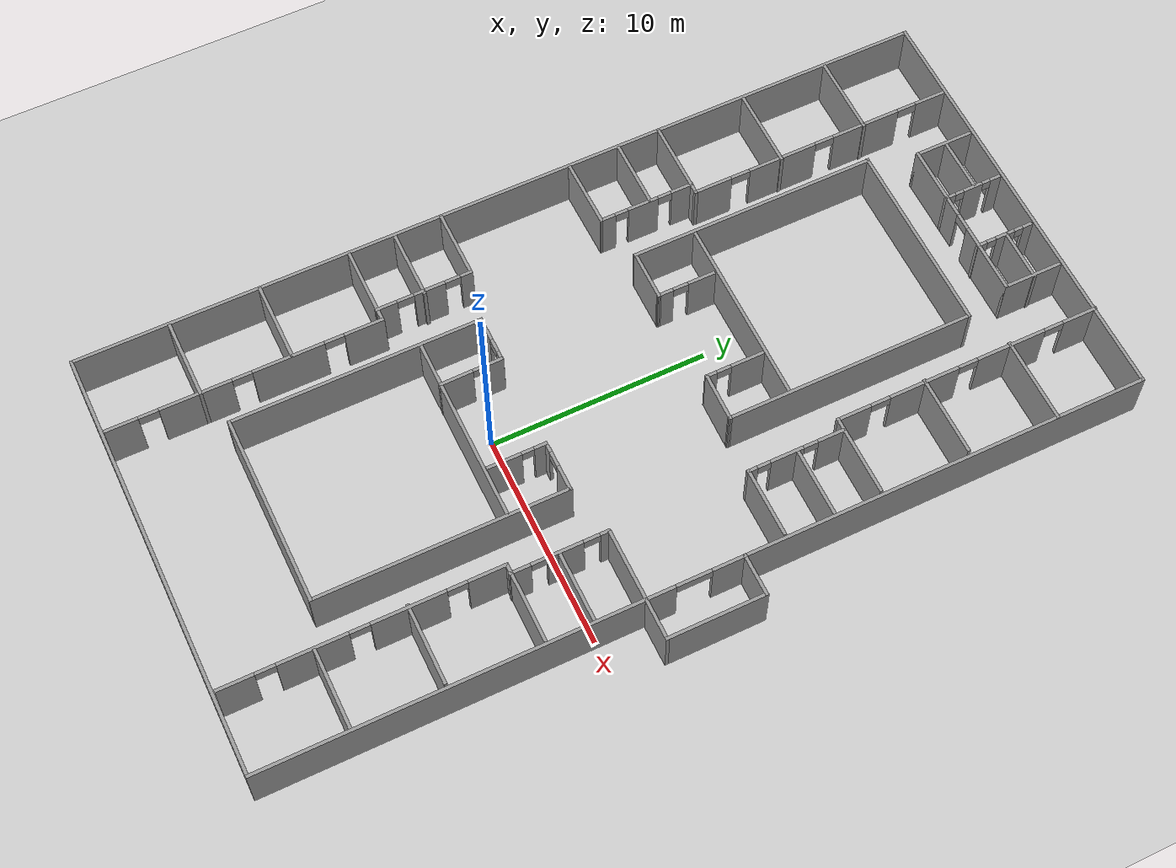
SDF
<sdf version="1.7">
 <world name="default">
  <light name="sun" type="directional">
   <pose>0 0 10 0 -0 0</pose>
   <diffuse>0.8 0.8 0.8 1</diffuse>
   <specular>0.2 0.2 0.2 1</specular>
   <attenuation>
    <range>1000</range>
    <constant>0.9</constant>
    <linear>0.01</linear>
    <quadratic>0.001</quadratic>
   </attenuation>
   <direction>-0.5 0.1 -0.9</direction>
   <spot><inner_angle>0</inner_angle><outer_angle>0</outer_angle><falloff>0</falloff></spot>
  </light>
  <model name="ground_plane">
   <static>1</static>
   <link name="link">
    <collision name="collision">
     <geometry><plane><normal>0 0 1</normal><size>100 100</size></plane></geometry>
     <surface><friction><ode><mu>100</mu><mu2>50</mu2></ode></friction></surface>
    </collision>
    <visual name="visual">
     <cast_shadows>0</cast_shadows>
     <geometry><plane><normal>0 0 1</normal><size>100 100</size></plane></geometry>
     <material>
      <script><uri>file://media/materials/scripts/gazebo.material</uri><name>Gazebo/Grey</name></script>
     </material>
    </visual>
   </link>
  </model>
  <gravity>0 0 -9.8</gravity>
  <magnetic_field>6e-06 2.3e-05 -4.2e-05</magnetic_field>
  <atmosphere type="adiabatic"/>
  <physics type="ode">
   <max_step_size>0.001</max_step_size>
   <real_time_factor>1</real_time_factor>
   <real_time_update_rate>1000</real_time_update_rate>
  </physics>
  <scene><ambient>0.4 0.4 0.4 1</ambient><background>0.7 0.7 0.7 1</background><shadows>1</shadows></scene>
  <audio><device>default</device></audio>
  <spherical_coordinates>
   <surface_model>EARTH_WGS84</surface_model>
   <latitude_deg>0</latitude_deg>
   <longitude_deg>0</longitude_deg>
   <elevation>0</elevation>
   <heading_deg>0</heading_deg>
  </spherical_coordinates>
  <model name="hospital_world">
   <pose>1.05255 5.28475 0 0 -0 0</pose>
   <link name="Wall_104">
    <collision name="Wall_104_Collision">
     <geometry><box><size>3.25 0.15 2.5</size></box></geometry>
     <pose>0 0 1.25 0 -0 0</pose>
    </collision>
    <visual name="Wall_104_Visual">
     <pose>0 0 1.25 0 -0 0</pose>
     <geometry><box><size>3.25 0.15 2.5</size></box></geometry>
     <material>
      <script><uri>file://media/materials/scripts/gazebo.material</uri><name>Gazebo/Grey</name></script>
      <ambient>1 1 1 1</ambient>
     </material>
     <meta><layer>0</layer></meta>
    </visual>
    <pose>-9.33553 5.41345 0 0 -0 0</pose>
   </link>
   <link name="Wall_107">
    <collision name="Wall_107_Collision">
     <geometry><box><size>2.75 0.15 2.5</size></box></geometry>
     <pose>0 0 1.25 0 -0 0</pose>
    </collision>
    <visual name="Wall_107_Visual">
     <pose>0 0 1.25 0 -0 0</pose>
     <geometry><box><size>2.75 0.15 2.5</size></box></geometry>
     <material>
      <script><uri>file://media/materials/scripts/gazebo.material</uri><name>Gazebo/Grey</name></script>
      <ambient>1 1 1 1</ambient>
     </material>
     <meta><layer>0</layer></meta>
    </visual>
    <pose>-4.86473 18.4237 0 0 -0 -1.5708</pose>
   </link>
   <link name="Wall_108">
    <pose>-1.06473 17.1237 0 0 -0 0</pose>
    <visual name="Wall_108_Visual_0">
     <pose>-2.06983 0 1.25 0 -0 0</pose>
     <geometry><box><size>3.61035 0.15 2.5</size></box></geometry>
     <material>
      <script><uri>file://media/materials/scripts/gazebo.material</uri><name>Gazebo/Grey</name></script>
      <ambient>1 1 1 1</ambient>
     </material>
     <meta><layer>0</layer></meta>
    </visual>
    <collision name="Wall_108_Collision_0">
     <geometry><box><size>3.61035 0.15 2.5</size></box></geometry>
     <pose>-2.06983 0 1.25 0 -0 0</pose>
    </collision>
    <visual name="Wall_108_Visual_1">
     <pose>2.20929 0 1.25 0 -0 0</pose>
     <geometry><box><size>3.33142 0.15 2.5</size></box></geometry>
     <material>
      <script><uri>file://media/materials/scripts/gazebo.material</uri><name>Gazebo/Grey</name></script>
      <ambient>1 1 1 1</ambient>
     </material>
     <meta><layer>0</layer></meta>
    </visual>
    <collision name="Wall_108_Collision_1">
     <geometry><box><size>3.33142 0.15 2.5</size></box></geometry>
     <pose>2.20929 0 1.25 0 -0 0</pose>
    </collision>
    <visual name="Wall_108_Visual_2">
     <pose>0.139461 0 2.25 0 -0 0</pose>
     <geometry><box><size>0.808229 0.15 0.5</size></box></geometry>
     <material>
      <script><uri>file://media/materials/scripts/gazebo.material</uri><name>Gazebo/Grey</name></script>
      <ambient>1 1 1 1</ambient>
     </material>
     <meta><layer>0</layer></meta>
    </visual>
    <collision name="Wall_108_Collision_2">
     <geometry><box><size>0.808229 0.15 0.5</size></box></geometry>
     <pose>0.139461 0 2.25 0 -0 0</pose>
    </collision>
   </link>
   <link name="Wall_109">
    <collision name="Wall_109_Collision">
     <geometry><box><size>2.75 0.15 2.5</size></box></geometry>
     <pose>0 0 1.25 0 -0 0</pose>
    </collision>
    <visual name="Wall_109_Visual">
     <pose>0 0 1.25 0 -0 0</pose>
     <geometry><box><size>2.75 0.15 2.5</size></box></geometry>
     <material>
      <script><uri>file://media/materials/scripts/gazebo.material</uri><name>Gazebo/Grey</name></script>
      <ambient>1 1 1 1</ambient>
     </material>
     <meta><layer>0</layer></meta>
    </visual>
    <pose>2.73527 18.4237 0 0 -0 1.5708</pose>
   </link>
   <link name="Wall_113">
    <collision name="Wall_113_Collision">
     <geometry><box><size>2.5 0.15 2.5</size></box></geometry>
     <pose>0 0 1.25 0 -0 0</pose>
    </collision>
    <visual name="Wall_113_Visual">
     <pose>0 0 1.25 0 -0 0</pose>
     <geometry><box><size>2.5 0.15 2.5</size></box></geometry>
     <material>
      <script><uri>file://media/materials/scripts/gazebo.material</uri><name>Gazebo/Grey</name></script>
      <ambient>1 1 1 1</ambient>
     </material>
     <meta><layer>0</layer></meta>
    </visual>
    <pose>-3.54473 18.5058 0 0 -0 0</pose>
   </link>
   <link name="Wall_115">
    <pose>-2.30971 18.4188 0 0 -0 -1.5708</pose>
    <visual name="Wall_115_Visual_0">
     <pose>-1.11227 0 1.25 0 -0 0</pose>
     <geometry><box><size>0.525457 0.15 2.5</size></box></geometry>
     <material>
      <script><uri>file://media/materials/scripts/gazebo.material</uri><name>Gazebo/Grey</name></script>
      <ambient>1 1 1 1</ambient>
     </material>
     <meta><layer>0</layer></meta>
    </visual>
    <collision name="Wall_115_Collision_0">
     <geometry><box><size>0.525457 0.15 2.5</size></box></geometry>
     <pose>-1.11227 0 1.25 0 -0 0</pose>
    </collision>
    <visual name="Wall_115_Visual_1">
     <pose>0.006111 0 1.25 0 -0 0</pose>
     <geometry><box><size>0.922114 0.15 2.5</size></box></geometry>
     <material>
      <script><uri>file://media/materials/scripts/gazebo.material</uri><name>Gazebo/Grey</name></script>
      <ambient>1 1 1 1</ambient>
     </material>
     <meta><layer>0</layer></meta>
    </visual>
    <collision name="Wall_115_Collision_1">
     <geometry><box><size>0.922114 0.15 2.5</size></box></geometry>
     <pose>0.006111 0 1.25 0 -0 0</pose>
    </collision>
    <visual name="Wall_115_Visual_2">
     <pose>1.12503 0 1.25 0 -0 0</pose>
     <geometry><box><size>0.499936 0.15 2.5</size></box></geometry>
     <material>
      <script><uri>file://media/materials/scripts/gazebo.material</uri><name>Gazebo/Grey</name></script>
      <ambient>1 1 1 1</ambient>
     </material>
     <meta><layer>0</layer></meta>
    </visual>
    <collision name="Wall_115_Collision_2">
     <geometry><box><size>0.499936 0.15 2.5</size></box></geometry>
     <pose>1.12503 0 1.25 0 -0 0</pose>
    </collision>
    <visual name="Wall_115_Visual_3">
     <pose>-0.652245 0 2.25 0 -0 0</pose>
     <geometry><box><size>0.394596 0.15 0.5</size></box></geometry>
     <material>
      <script><uri>file://media/materials/scripts/gazebo.material</uri><name>Gazebo/Grey</name></script>
      <ambient>1 1 1 1</ambient>
     </material>
     <meta><layer>0</layer></meta>
    </visual>
    <collision name="Wall_115_Collision_3">
     <geometry><box><size>0.394596 0.15 0.5</size></box></geometry>
     <pose>-0.652245 0 2.25 0 -0 0</pose>
    </collision>
    <visual name="Wall_115_Visual_4">
     <pose>0.671116 0 2.25 0 -0 0</pose>
     <geometry><box><size>0.407896 0.15 0.5</size></box></geometry>
     <material>
      <script><uri>file://media/materials/scripts/gazebo.material</uri><name>Gazebo/Grey</name></script>
      <ambient>1 1 1 1</ambient>
     </material>
     <meta><layer>0</layer></meta>
    </visual>
    <collision name="Wall_115_Collision_4">
     <geometry><box><size>0.407896 0.15 0.5</size></box></geometry>
     <pose>0.671116 0 2.25 0 -0 0</pose>
    </collision>
   </link>
   <link name="Wall_117">
    <pose>0.430111 18.3922 0 0 -0 -1.5708</pose>
    <visual name="Wall_117_Visual_0">
     <pose>-1.13887 0 1.25 0 -0 0</pose>
     <geometry><box><size>0.472258 0.15 2.5</size></box></geometry>
     <material>
      <script><uri>file://media/materials/scripts/gazebo.material</uri><name>Gazebo/Grey</name></script>
      <ambient>1 1 1 1</ambient>
     </material>
     <meta><layer>0</layer></meta>
    </visual>
    <collision name="Wall_117_Collision_0">
     <geometry><box><size>0.472258 0.15 2.5</size></box></geometry>
     <pose>-1.13887 0 1.25 0 -0 0</pose>
    </collision>
    <visual name="Wall_117_Visual_1">
     <pose>-0.033788 0 1.25 0 -0 0</pose>
     <geometry><box><size>0.922114 0.15 2.5</size></box></geometry>
     <material>
      <script><uri>file://media/materials/scripts/gazebo.material</uri><name>Gazebo/Grey</name></script>
      <ambient>1 1 1 1</ambient>
     </material>
     <meta><layer>0</layer></meta>
    </visual>
    <collision name="Wall_117_Collision_1">
     <geometry><box><size>0.922114 0.15 2.5</size></box></geometry>
     <pose>-0.033788 0 1.25 0 -0 0</pose>
    </collision>
    <visual name="Wall_117_Visual_2">
     <pose>1.12503 0 1.25 0 -0 0</pose>
     <geometry><box><size>0.499935 0.15 2.5</size></box></geometry>
     <material>
      <script><uri>file://media/materials/scripts/gazebo.material</uri><name>Gazebo/Grey</name></script>
      <ambient>1 1 1 1</ambient>
     </material>
     <meta><layer>0</layer></meta>
    </visual>
    <collision name="Wall_117_Collision_2">
     <geometry><box><size>0.499935 0.15 2.5</size></box></geometry>
     <pose>1.12503 0 1.25 0 -0 0</pose>
    </collision>
    <visual name="Wall_117_Visual_3">
     <pose>-0.698793 0 2.25 0 -0 0</pose>
     <geometry><box><size>0.407896 0.15 0.5</size></box></geometry>
     <material>
      <script><uri>file://media/materials/scripts/gazebo.material</uri><name>Gazebo/Grey</name></script>
      <ambient>1 1 1 1</ambient>
     </material>
     <meta><layer>0</layer></meta>
    </visual>
    <collision name="Wall_117_Collision_3">
     <geometry><box><size>0.407896 0.15 0.5</size></box></geometry>
     <pose>-0.698793 0 2.25 0 -0 0</pose>
    </collision>
    <visual name="Wall_117_Visual_4">
     <pose>0.651167 0 2.25 0 -0 0</pose>
     <geometry><box><size>0.447797 0.15 0.5</size></box></geometry>
     <material>
      <script><uri>file://media/materials/scripts/gazebo.material</uri><name>Gazebo/Grey</name></script>
      <ambient>1 1 1 1</ambient>
     </material>
     <meta><layer>0</layer></meta>
    </visual>
    <collision name="Wall_117_Collision_4">
     <geometry><box><size>0.447797 0.15 0.5</size></box></geometry>
     <pose>0.651167 0 2.25 0 -0 0</pose>
    </collision>
   </link>
   <link name="Wall_119">
    <collision name="Wall_119_Collision">
     <geometry><box><size>2.5 0.15 2.5</size></box></geometry>
     <pose>0 0 1.25 0 -0 0</pose>
    </collision>
    <visual name="Wall_119_Visual">
     <pose>0 0 1.25 0 -0 0</pose>
     <geometry><box><size>2.5 0.15 2.5</size></box></geometry>
     <material>
      <script><uri>file://media/materials/scripts/gazebo.material</uri><name>Gazebo/Grey</name></script>
      <ambient>1 1 1 1</ambient>
     </material>
     <meta><layer>0</layer></meta>
    </visual>
    <pose>1.60511 18.4792 0 0 -0 0</pose>
   </link>
   <link name="Wall_13">
    <collision name="Wall_13_Collision">
     <geometry><box><size>40 0.15 2.5</size></box></geometry>
     <pose>0 0 1.25 0 -0 0</pose>
    </collision>
    <visual name="Wall_13_Visual">
     <pose>0 0 1.25 0 -0 0</pose>
     <geometry><box><size>40 0.15 2.5</size></box></geometry>
     <material>
      <script><uri>file://media/materials/scripts/gazebo.material</uri><name>Gazebo/Grey</name></script>
      <ambient>1 1 1 1</ambient>
     </material>
     <meta><layer>0</layer></meta>
    </visual>
    <pose>-10.975 -0.021727 0 0 -0 -1.5708</pose>
   </link>
   <link name="Wall_131">
    <collision name="Wall_131_Collision">
     <geometry><box><size>11.5 0.15 2.5</size></box></geometry>
     <pose>0 0 1.25 0 -0 0</pose>
    </collision>
    <visual name="Wall_131_Visual">
     <pose>0 0 1.25 0 -0 0</pose>
     <geometry><box><size>11.5 0.15 2.5</size></box></geometry>
     <material>
      <script><uri>file://media/materials/scripts/gazebo.material</uri><name>Gazebo/Grey</name></script>
      <ambient>1 1 1 1</ambient>
     </material>
     <meta><layer>0</layer></meta>
    </visual>
    <pose>-5.53184 9.2924 0 0 -0 -1.5708</pose>
   </link>
   <link name="Wall_133">
    <collision name="Wall_133_Collision">
     <geometry><box><size>11.5 0.15 2.5</size></box></geometry>
     <pose>0 0 1.25 0 -0 0</pose>
    </collision>
    <visual name="Wall_133_Visual">
     <pose>0 0 1.25 0 -0 0</pose>
     <geometry><box><size>11.5 0.15 2.5</size></box></geometry>
     <material>
      <script><uri>file://media/materials/scripts/gazebo.material</uri><name>Gazebo/Grey</name></script>
      <ambient>1 1 1 1</ambient>
     </material>
     <meta><layer>0</layer></meta>
    </visual>
    <pose>3.30287 9.2924 0 0 -0 1.5708</pose>
   </link>
   <link name="Wall_134">
    <collision name="Wall_134_Collision">
     <geometry><box><size>9 0.15 2.5</size></box></geometry>
     <pose>0 0 1.25 0 -0 0</pose>
    </collision>
    <visual name="Wall_134_Visual">
     <pose>0 0 1.25 0 -0 0</pose>
     <geometry><box><size>9 0.15 2.5</size></box></geometry>
     <material>
      <script><uri>file://media/materials/scripts/gazebo.material</uri><name>Gazebo/Grey</name></script>
      <ambient>1 1 1 1</ambient>
     </material>
     <meta><layer>0</layer></meta>
    </visual>
    <pose>-1.12213 14.9674 0 0 -0 3.14159</pose>
   </link>
   <link name="Wall_136">
    <collision name="Wall_136_Collision">
     <geometry><box><size>8.75 0.15 2.5</size></box></geometry>
     <pose>0 0 1.25 0 -0 0</pose>
    </collision>
    <visual name="Wall_136_Visual">
     <pose>0 0 1.25 0 -0 0</pose>
     <geometry><box><size>8.75 0.15 2.5</size></box></geometry>
     <material>
      <script><uri>file://media/materials/scripts/gazebo.material</uri><name>Gazebo/Grey</name></script>
      <ambient>1 1 1 1</ambient>
     </material>
     <meta><layer>0</layer></meta>
    </visual>
    <pose>-1.06193 6.42009 0 0 -0 0</pose>
   </link>
   <link name="Wall_14">
    <collision name="Wall_14_Collision">
     <geometry><box><size>20.25 0.15 2.5</size></box></geometry>
     <pose>0 0 1.25 0 -0 0</pose>
    </collision>
    <visual name="Wall_14_Visual">
     <pose>0 0 1.25 0 -0 0</pose>
     <geometry><box><size>20.25 0.15 2.5</size></box></geometry>
     <material>
      <script><uri>file://media/materials/scripts/gazebo.material</uri><name>Gazebo/Grey</name></script>
      <ambient>1 1 1 1</ambient>
     </material>
     <meta><layer>0</layer></meta>
    </visual>
    <pose>-0.924999 -19.9467 0 0 -0 0</pose>
   </link>
   <link name="Wall_140">
    <pose>-3.33273 -5.09193 0 0 -0 -1.55784</pose>
    <visual name="Wall_140_Visual_0">
     <pose>-1.10334 0 1.25 0 -0 0</pose>
     <geometry><box><size>0.735345 0.15 2.5</size></box></geometry>
     <material>
      <script><uri>file://media/materials/scripts/gazebo.material</uri><name>Gazebo/Grey</name></script>
      <ambient>1 1 1 1</ambient>
     </material>
     <meta><layer>0</layer></meta>
    </visual>
    <collision name="Wall_140_Collision_0">
     <geometry><box><size>0.735345 0.15 2.5</size></box></geometry>
     <pose>-1.10334 0 1.25 0 -0 0</pose>
    </collision>
    <visual name="Wall_140_Visual_1">
     <pose>0.701176 0 1.25 0 -0 0</pose>
     <geometry><box><size>1.53968 0.15 2.5</size></box></geometry>
     <material>
      <script><uri>file://media/materials/scripts/gazebo.material</uri><name>Gazebo/Grey</name></script>
      <ambient>1 1 1 1</ambient>
     </material>
     <meta><layer>0</layer></meta>
    </visual>
    <collision name="Wall_140_Collision_1">
     <geometry><box><size>1.53968 0.15 2.5</size></box></geometry>
     <pose>0.701176 0 1.25 0 -0 0</pose>
    </collision>
    <visual name="Wall_140_Visual_2">
     <pose>-0.402168 0 2.25 0 -0 0</pose>
     <geometry><box><size>0.667007 0.15 0.5</size></box></geometry>
     <material>
      <script><uri>file://media/materials/scripts/gazebo.material</uri><name>Gazebo/Grey</name></script>
      <ambient>1 1 1 1</ambient>
     </material>
     <meta><layer>0</layer></meta>
    </visual>
    <collision name="Wall_140_Collision_2">
     <geometry><box><size>0.667007 0.15 0.5</size></box></geometry>
     <pose>-0.402168 0 2.25 0 -0 0</pose>
    </collision>
   </link>
   <link name="Wall_142">
    <pose>1.08598 -5.01489 0 0 -0 -1.5708</pose>
    <visual name="Wall_142_Visual_0">
     <pose>-1.06401 0 1.25 0 -0 0</pose>
     <geometry><box><size>0.621972 0.15 2.5</size></box></geometry>
     <material>
      <script><uri>file://media/materials/scripts/gazebo.material</uri><name>Gazebo/Grey</name></script>
      <ambient>1 1 1 1</ambient>
     </material>
     <meta><layer>0</layer></meta>
    </visual>
    <collision name="Wall_142_Collision_0">
     <geometry><box><size>0.621972 0.15 2.5</size></box></geometry>
     <pose>-1.06401 0 1.25 0 -0 0</pose>
    </collision>
    <visual name="Wall_142_Visual_1">
     <pose>0.586521 0 1.25 0 -0 0</pose>
     <geometry><box><size>1.57696 0.15 2.5</size></box></geometry>
     <material>
      <script><uri>file://media/materials/scripts/gazebo.material</uri><name>Gazebo/Grey</name></script>
      <ambient>1 1 1 1</ambient>
     </material>
     <meta><layer>0</layer></meta>
    </visual>
    <collision name="Wall_142_Collision_1">
     <geometry><box><size>1.57696 0.15 2.5</size></box></geometry>
     <pose>0.586521 0 1.25 0 -0 0</pose>
    </collision>
    <visual name="Wall_142_Visual_2">
     <pose>-0.477493 0 2.25 0 -0 0</pose>
     <geometry><box><size>0.551071 0.15 0.5</size></box></geometry>
     <material>
      <script><uri>file://media/materials/scripts/gazebo.material</uri><name>Gazebo/Grey</name></script>
      <ambient>1 1 1 1</ambient>
     </material>
     <meta><layer>0</layer></meta>
    </visual>
    <collision name="Wall_142_Collision_2">
     <geometry><box><size>0.551071 0.15 0.5</size></box></geometry>
     <pose>-0.477493 0 2.25 0 -0 0</pose>
    </collision>
   </link>
   <link name="Wall_144">
    <pose>-3.27395 4.90802 0 0 -0 -1.5708</pose>
    <visual name="Wall_144_Visual_0">
     <pose>-0.725746 0 1.25 0 -0 0</pose>
     <geometry><box><size>1.29851 0.15 2.5</size></box></geometry>
     <material>
      <script><uri>file://media/materials/scripts/gazebo.material</uri><name>Gazebo/Grey</name></script>
      <ambient>1 1 1 1</ambient>
     </material>
     <meta><layer>0</layer></meta>
    </visual>
    <collision name="Wall_144_Collision_0">
     <geometry><box><size>1.29851 0.15 2.5</size></box></geometry>
     <pose>-0.725746 0 1.25 0 -0 0</pose>
    </collision>
    <visual name="Wall_144_Visual_1">
     <pose>1.00095 0 1.25 0 -0 0</pose>
     <geometry><box><size>0.748103 0.15 2.5</size></box></geometry>
     <material>
      <script><uri>file://media/materials/scripts/gazebo.material</uri><name>Gazebo/Grey</name></script>
      <ambient>1 1 1 1</ambient>
     </material>
     <meta><layer>0</layer></meta>
    </visual>
    <collision name="Wall_144_Collision_1">
     <geometry><box><size>0.748103 0.15 2.5</size></box></geometry>
     <pose>1.00095 0 1.25 0 -0 0</pose>
    </collision>
    <visual name="Wall_144_Visual_2">
     <pose>0.275202 0 2.25 0 -0 0</pose>
     <geometry><box><size>0.70339 0.15 0.5</size></box></geometry>
     <material>
      <script><uri>file://media/materials/scripts/gazebo.material</uri><name>Gazebo/Grey</name></script>
      <ambient>1 1 1 1</ambient>
     </material>
     <meta><layer>0</layer></meta>
    </visual>
    <collision name="Wall_144_Collision_2">
     <geometry><box><size>0.70339 0.15 0.5</size></box></geometry>
     <pose>0.275202 0 2.25 0 -0 0</pose>
    </collision>
   </link>
   <link name="Wall_146">
    <pose>1.13162 4.96027 0 0 -0 -1.5708</pose>
    <visual name="Wall_146_Visual_0">
     <pose>-0.595533 0 1.25 0 -0 0</pose>
     <geometry><box><size>1.55893 0.15 2.5</size></box></geometry>
     <material>
      <script><uri>file://media/materials/scripts/gazebo.material</uri><name>Gazebo/Grey</name></script>
      <ambient>1 1 1 1</ambient>
     </material>
     <meta><layer>0</layer></meta>
    </visual>
    <collision name="Wall_146_Collision_0">
     <geometry><box><size>1.55893 0.15 2.5</size></box></geometry>
     <pose>-0.595533 0 1.25 0 -0 0</pose>
    </collision>
    <visual name="Wall_146_Visual_1">
     <pose>1.10803 0 1.25 0 -0 0</pose>
     <geometry><box><size>0.533938 0.15 2.5</size></box></geometry>
     <material>
      <script><uri>file://media/materials/scripts/gazebo.material</uri><name>Gazebo/Grey</name></script>
      <ambient>1 1 1 1</ambient>
     </material>
     <meta><layer>0</layer></meta>
    </visual>
    <collision name="Wall_146_Collision_1">
     <geometry><box><size>0.533938 0.15 2.5</size></box></geometry>
     <pose>1.10803 0 1.25 0 -0 0</pose>
    </collision>
    <visual name="Wall_146_Visual_2">
     <pose>0.512498 0 2.25 0 -0 0</pose>
     <geometry><box><size>0.657129 0.15 0.5</size></box></geometry>
     <material>
      <script><uri>file://media/materials/scripts/gazebo.material</uri><name>Gazebo/Grey</name></script>
      <ambient>1 1 1 1</ambient>
     </material>
     <meta><layer>0</layer></meta>
    </visual>
    <collision name="Wall_146_Collision_2">
     <geometry><box><size>0.657129 0.15 0.5</size></box></geometry>
     <pose>0.512498 0 2.25 0 -0 0</pose>
    </collision>
   </link>
   <link name="Wall_148">
    <collision name="Wall_148_Collision">
     <geometry><box><size>2.32167 0.15 2.5</size></box></geometry>
     <pose>0 0 1.25 0 -0 0</pose>
    </collision>
    <visual name="Wall_148_Visual">
     <pose>0 0 1.25 0 -0 0</pose>
     <geometry><box><size>2.32167 0.15 2.5</size></box></geometry>
     <material>
      <script><uri>file://media/materials/scripts/gazebo.material</uri><name>Gazebo/Grey</name></script>
      <ambient>1 1 1 1</ambient>
     </material>
     <meta><layer>0</layer></meta>
    </visual>
    <pose>2.21725 3.63883 0 0 -0 -0.019743</pose>
   </link>
   <link name="Wall_15">
    <collision name="Wall_15_Collision">
     <geometry><box><size>17 0.15 2.5</size></box></geometry>
     <pose>0 0 1.25 0 -0 0</pose>
    </collision>
    <visual name="Wall_15_Visual">
     <pose>0 0 1.25 0 -0 0</pose>
     <geometry><box><size>17 0.15 2.5</size></box></geometry>
     <material>
      <script><uri>file://media/materials/scripts/gazebo.material</uri><name>Gazebo/Grey</name></script>
      <ambient>1 1 1 1</ambient>
     </material>
     <meta><layer>0</layer></meta>
    </visual>
    <pose>9.125 -11.5217 0 0 -0 1.5708</pose>
   </link>
   <link name="Wall_150">
    <collision name="Wall_150_Collision">
     <geometry><box><size>2.4079 0.15 2.5</size></box></geometry>
     <pose>0 0 1.25 0 -0 0</pose>
    </collision>
    <visual name="Wall_150_Visual">
     <pose>0 0 1.25 0 -0 0</pose>
     <geometry><box><size>2.4079 0.15 2.5</size></box></geometry>
     <material>
      <script><uri>file://media/materials/scripts/gazebo.material</uri><name>Gazebo/Grey</name></script>
      <ambient>1 1 1 1</ambient>
     </material>
     <meta><layer>0</layer></meta>
    </visual>
    <pose>-4.4029 3.61271 0 0 -0 -0.004153</pose>
   </link>
   <link name="Wall_152">
    <collision name="Wall_152_Collision">
     <geometry><box><size>8.75 0.15 2.5</size></box></geometry>
     <pose>0 0 1.25 0 -0 0</pose>
    </collision>
    <visual name="Wall_152_Visual">
     <pose>0 0 1.25 0 -0 0</pose>
     <geometry><box><size>8.75 0.15 2.5</size></box></geometry>
     <material>
      <script><uri>file://media/materials/scripts/gazebo.material</uri><name>Gazebo/Grey</name></script>
      <ambient>1 1 1 1</ambient>
     </material>
     <meta><layer>0</layer></meta>
    </visual>
    <pose>-1.00117 -6.47614 0 0 -0 0</pose>
   </link>
   <link name="Wall_154">
    <pose>-4.40742 -3.68941 0 0 -0 0</pose>
    <visual name="Wall_154_Visual_0">
     <pose>-0.547357 0 1.25 0 -0 0</pose>
     <geometry><box><size>1.15529 0.15 2.5</size></box></geometry>
     <material>
      <script><uri>file://media/materials/scripts/gazebo.material</uri><name>Gazebo/Grey</name></script>
      <ambient>1 1 1 1</ambient>
     </material>
     <meta><layer>0</layer></meta>
    </visual>
    <collision name="Wall_154_Collision_0">
     <geometry><box><size>1.15529 0.15 2.5</size></box></geometry>
     <pose>-0.547357 0 1.25 0 -0 0</pose>
    </collision>
    <visual name="Wall_154_Visual_1">
     <pose>0.899702 0 1.25 0 -0 0</pose>
     <geometry><box><size>0.450596 0.15 2.5</size></box></geometry>
     <material>
      <script><uri>file://media/materials/scripts/gazebo.material</uri><name>Gazebo/Grey</name></script>
      <ambient>1 1 1 1</ambient>
     </material>
     <meta><layer>0</layer></meta>
    </visual>
    <collision name="Wall_154_Collision_1">
     <geometry><box><size>0.450596 0.15 2.5</size></box></geometry>
     <pose>0.899702 0 1.25 0 -0 0</pose>
    </collision>
    <visual name="Wall_154_Visual_2">
     <pose>0.352345 0 2.25 0 -0 0</pose>
     <geometry><box><size>0.644118 0.15 0.5</size></box></geometry>
     <material>
      <script><uri>file://media/materials/scripts/gazebo.material</uri><name>Gazebo/Grey</name></script>
      <ambient>1 1 1 1</ambient>
     </material>
     <meta><layer>0</layer></meta>
    </visual>
    <collision name="Wall_154_Collision_2">
     <geometry><box><size>0.644118 0.15 0.5</size></box></geometry>
     <pose>0.352345 0 2.25 0 -0 0</pose>
    </collision>
   </link>
   <link name="Wall_156">
    <pose>2.30006 -3.70371 0 0 -0 3.14159</pose>
    <visual name="Wall_156_Visual_0">
     <pose>-0.537944 0 1.25 0 -0 0</pose>
     <geometry><box><size>1.17411 0.15 2.5</size></box></geometry>
     <material>
      <script><uri>file://media/materials/scripts/gazebo.material</uri><name>Gazebo/Grey</name></script>
      <ambient>1 1 1 1</ambient>
     </material>
     <meta><layer>0</layer></meta>
    </visual>
    <collision name="Wall_156_Collision_0">
     <geometry><box><size>1.17411 0.15 2.5</size></box></geometry>
     <pose>-0.537944 0 1.25 0 -0 0</pose>
    </collision>
    <visual name="Wall_156_Visual_1">
     <pose>0.944008 0 1.25 0 -0 0</pose>
     <geometry><box><size>0.361984 0.15 2.5</size></box></geometry>
     <material>
      <script><uri>file://media/materials/scripts/gazebo.material</uri><name>Gazebo/Grey</name></script>
      <ambient>1 1 1 1</ambient>
     </material>
     <meta><layer>0</layer></meta>
    </visual>
    <collision name="Wall_156_Collision_1">
     <geometry><box><size>0.361984 0.15 2.5</size></box></geometry>
     <pose>0.944008 0 1.25 0 -0 0</pose>
    </collision>
    <visual name="Wall_156_Visual_2">
     <pose>0.406064 0 2.25 0 -0 0</pose>
     <geometry><box><size>0.713904 0.15 0.5</size></box></geometry>
     <material>
      <script><uri>file://media/materials/scripts/gazebo.material</uri><name>Gazebo/Grey</name></script>
      <ambient>1 1 1 1</ambient>
     </material>
     <meta><layer>0</layer></meta>
    </visual>
    <collision name="Wall_156_Collision_2">
     <geometry><box><size>0.713904 0.15 0.5</size></box></geometry>
     <pose>0.406064 0 2.25 0 -0 0</pose>
    </collision>
   </link>
   <link name="Wall_158">
    <pose>9.125 -0.896727 0 0 -0 -1.5708</pose>
    <visual name="Wall_158_Visual_0">
     <pose>-1.49805 0 1.25 0 -0 0</pose>
     <geometry><box><size>1.55389 0.15 2.5</size></box></geometry>
     <material>
      <script><uri>file://media/materials/scripts/gazebo.material</uri><name>Gazebo/Grey</name></script>
      <ambient>1 1 1 1</ambient>
     </material>
     <meta><layer>0</layer></meta>
    </visual>
    <collision name="Wall_158_Collision_0">
     <geometry><box><size>1.55389 0.15 2.5</size></box></geometry>
     <pose>-1.49805 0 1.25 0 -0 0</pose>
    </collision>
    <visual name="Wall_158_Visual_1">
     <pose>1.57587 0 1.25 0 -0 0</pose>
     <geometry><box><size>1.39825 0.15 2.5</size></box></geometry>
     <material>
      <script><uri>file://media/materials/scripts/gazebo.material</uri><name>Gazebo/Grey</name></script>
      <ambient>1 1 1 1</ambient>
     </material>
     <meta><layer>0</layer></meta>
    </visual>
    <collision name="Wall_158_Collision_1">
     <geometry><box><size>1.39825 0.15 2.5</size></box></geometry>
     <pose>1.57587 0 1.25 0 -0 0</pose>
    </collision>
    <visual name="Wall_158_Visual_2">
     <pose>0.07782 0 2.25 0 -0 0</pose>
     <geometry><box><size>1.59786 0.15 0.5</size></box></geometry>
     <material>
      <script><uri>file://media/materials/scripts/gazebo.material</uri><name>Gazebo/Grey</name></script>
      <ambient>1 1 1 1</ambient>
     </material>
     <meta><layer>0</layer></meta>
    </visual>
    <collision name="Wall_158_Collision_2">
     <geometry><box><size>1.59786 0.15 0.5</size></box></geometry>
     <pose>0.07782 0 2.25 0 -0 0</pose>
    </collision>
   </link>
   <link name="Wall_16">
    <collision name="Wall_16_Collision">
     <geometry><box><size>2 0.15 2.5</size></box></geometry>
     <pose>0 0 1.25 0 -0 0</pose>
    </collision>
    <visual name="Wall_16_Visual">
     <pose>0 0 1.25 0 -0 0</pose>
     <geometry><box><size>2 0.15 2.5</size></box></geometry>
     <material>
      <script><uri>file://media/materials/scripts/gazebo.material</uri><name>Gazebo/Grey</name></script>
      <ambient>1 1 1 1</ambient>
     </material>
     <meta><layer>0</layer></meta>
    </visual>
    <pose>10.05 -3.09673 0 0 -0 0</pose>
   </link>
   <link name="Wall_165">
    <collision name="Wall_165_Collision">
     <geometry><box><size>4.55 0.15 2.5</size></box></geometry>
     <pose>0 0 1.25 0 -0 0</pose>
    </collision>
    <visual name="Wall_165_Visual">
     <pose>0 0 1.25 0 -0 0</pose>
     <geometry><box><size>4.55 0.15 2.5</size></box></geometry>
     <material>
      <script><uri>file://media/materials/scripts/gazebo.material</uri><name>Gazebo/Grey</name></script>
      <ambient>1 1 1 1</ambient>
     </material>
     <meta><layer>0</layer></meta>
    </visual>
    <pose>10.975 -0.896727 0 0 -0 -1.5708</pose>
   </link>
   <link name="Wall_18">
    <pose>-7.31204 13.579 0 0 -0 -1.5708</pose>
    <visual name="Wall_18_Visual_0">
     <pose>-5.51242 0 1.25 0 -0 0</pose>
     <geometry><box><size>1.47516 0.15 2.5</size></box></geometry>
     <material>
      <script><uri>file://media/materials/scripts/gazebo.material</uri><name>Gazebo/Grey</name></script>
      <ambient>1 1 1 1</ambient>
     </material>
     <meta><layer>0</layer></meta>
    </visual>
    <collision name="Wall_18_Collision_0">
     <geometry><box><size>1.47516 0.15 2.5</size></box></geometry>
     <pose>-5.51242 0 1.25 0 -0 0</pose>
    </collision>
    <visual name="Wall_18_Visual_1">
     <pose>-2.24943 0 1.25 0 -0 0</pose>
     <geometry><box><size>3.25082 0.15 2.5</size></box></geometry>
     <material>
      <script><uri>file://media/materials/scripts/gazebo.material</uri><name>Gazebo/Grey</name></script>
      <ambient>1 1 1 1</ambient>
     </material>
     <meta><layer>0</layer></meta>
    </visual>
    <collision name="Wall_18_Collision_1">
     <geometry><box><size>3.25082 0.15 2.5</size></box></geometry>
     <pose>-2.24943 0 1.25 0 -0 0</pose>
    </collision>
    <visual name="Wall_18_Visual_2">
     <pose>1.90958 0 1.25 0 -0 0</pose>
     <geometry><box><size>3.2672 0.15 2.5</size></box></geometry>
     <material>
      <script><uri>file://media/materials/scripts/gazebo.material</uri><name>Gazebo/Grey</name></script>
      <ambient>1 1 1 1</ambient>
     </material>
     <meta><layer>0</layer></meta>
    </visual>
    <collision name="Wall_18_Collision_2">
     <geometry><box><size>3.2672 0.15 2.5</size></box></geometry>
     <pose>1.90958 0 1.25 0 -0 0</pose>
    </collision>
    <visual name="Wall_18_Visual_3">
     <pose>5.34659 0 1.25 0 -0 0</pose>
     <geometry><box><size>1.80682 0.15 2.5</size></box></geometry>
     <material>
      <script><uri>file://media/materials/scripts/gazebo.material</uri><name>Gazebo/Grey</name></script>
      <ambient>1 1 1 1</ambient>
     </material>
     <meta><layer>0</layer></meta>
    </visual>
    <collision name="Wall_18_Collision_3">
     <geometry><box><size>1.80682 0.15 2.5</size></box></geometry>
     <pose>5.34659 0 1.25 0 -0 0</pose>
    </collision>
    <visual name="Wall_18_Visual_4">
     <pose>-4.32484 0 2.25 0 -0 0</pose>
     <geometry><box><size>0.9 0.15 0.5</size></box></geometry>
     <material>
      <script><uri>file://media/materials/scripts/gazebo.material</uri><name>Gazebo/Grey</name></script>
      <ambient>1 1 1 1</ambient>
     </material>
     <meta><layer>0</layer></meta>
    </visual>
    <collision name="Wall_18_Collision_4">
     <geometry><box><size>0.9 0.15 0.5</size></box></geometry>
     <pose>-4.32484 0 2.25 0 -0 0</pose>
    </collision>
    <visual name="Wall_18_Visual_5">
     <pose>-0.174016 0 2.25 0 -0 0</pose>
     <geometry><box><size>0.9 0.15 0.5</size></box></geometry>
     <material>
      <script><uri>file://media/materials/scripts/gazebo.material</uri><name>Gazebo/Grey</name></script>
      <ambient>1 1 1 1</ambient>
     </material>
     <meta><layer>0</layer></meta>
    </visual>
    <collision name="Wall_18_Collision_5">
     <geometry><box><size>0.9 0.15 0.5</size></box></geometry>
     <pose>-0.174016 0 2.25 0 -0 0</pose>
    </collision>
    <visual name="Wall_18_Visual_6">
     <pose>3.99318 0 2.25 0 -0 0</pose>
     <geometry><box><size>0.9 0.15 0.5</size></box></geometry>
     <material>
      <script><uri>file://media/materials/scripts/gazebo.material</uri><name>Gazebo/Grey</name></script>
      <ambient>1 1 1 1</ambient>
     </material>
     <meta><layer>0</layer></meta>
    </visual>
    <collision name="Wall_18_Collision_6">
     <geometry><box><size>0.9 0.15 0.5</size></box></geometry>
     <pose>3.99318 0 2.25 0 -0 0</pose>
    </collision>
   </link>
   <link name="Wall_186">
    <collision name="Wall_186_Collision">
     <geometry><box><size>11.5 0.15 2.5</size></box></geometry>
     <pose>0 0 1.25 0 -0 0</pose>
    </collision>
    <visual name="Wall_186_Visual">
     <pose>0 0 1.25 0 -0 0</pose>
     <geometry><box><size>11.5 0.15 2.5</size></box></geometry>
     <material>
      <script><uri>file://media/materials/scripts/gazebo.material</uri><name>Gazebo/Grey</name></script>
      <ambient>1 1 1 1</ambient>
     </material>
     <meta><layer>0</layer></meta>
    </visual>
    <pose>-5.45742 -9.36441 0 0 -0 -1.5708</pose>
   </link>
   <link name="Wall_187">
    <collision name="Wall_187_Collision">
     <geometry><box><size>9 0.15 2.5</size></box></geometry>
     <pose>0 0 1.25 0 -0 0</pose>
    </collision>
    <visual name="Wall_187_Visual">
     <pose>0 0 1.25 0 -0 0</pose>
     <geometry><box><size>9 0.15 2.5</size></box></geometry>
     <material>
      <script><uri>file://media/materials/scripts/gazebo.material</uri><name>Gazebo/Grey</name></script>
      <ambient>1 1 1 1</ambient>
     </material>
     <meta><layer>0</layer></meta>
    </visual>
    <pose>-1.03242 -15.0394 0 0 -0 0</pose>
   </link>
   <link name="Wall_19">
    <collision name="Wall_19_Collision">
     <geometry><box><size>3.75 0.15 2.5</size></box></geometry>
     <pose>0 0 1.25 0 -0 0</pose>
    </collision>
    <visual name="Wall_19_Visual">
     <pose>0 0 1.25 0 -0 0</pose>
     <geometry><box><size>3.75 0.15 2.5</size></box></geometry>
     <material>
      <script><uri>file://media/materials/scripts/gazebo.material</uri><name>Gazebo/Grey</name></script>
      <ambient>1 1 1 1</ambient>
     </material>
     <meta><layer>0</layer></meta>
    </visual>
    <pose>-9.11204 7.40401 0 0 -0 3.14159</pose>
   </link>
   <link name="Wall_196">
    <collision name="Wall_196_Collision">
     <geometry><box><size>11.5 0.15 2.5</size></box></geometry>
     <pose>0 0 1.25 0 -0 0</pose>
    </collision>
    <visual name="Wall_196_Visual">
     <pose>0 0 1.25 0 -0 0</pose>
     <geometry><box><size>11.5 0.15 2.5</size></box></geometry>
     <material>
      <script><uri>file://media/materials/scripts/gazebo.material</uri><name>Gazebo/Grey</name></script>
      <ambient>1 1 1 1</ambient>
     </material>
     <meta><layer>0</layer></meta>
    </visual>
    <pose>3.39258 -9.36441 0 0 -0 1.5708</pose>
   </link>
   <link name="Wall_21">
    <pose>-7.76807 5.23849 0 0 -0 -1.5708</pose>
    <visual name="Wall_21_Visual_0">
     <pose>-1.71434 0 1.25 0 -0 0</pose>
     <geometry><box><size>1.07133 0.15 2.5</size></box></geometry>
     <material>
      <script><uri>file://media/materials/scripts/gazebo.material</uri><name>Gazebo/Grey</name></script>
      <ambient>1 1 1 1</ambient>
     </material>
     <meta><layer>0</layer></meta>
    </visual>
    <collision name="Wall_21_Collision_0">
     <geometry><box><size>1.07133 0.15 2.5</size></box></geometry>
     <pose>-1.71434 0 1.25 0 -0 0</pose>
    </collision>
    <visual name="Wall_21_Visual_1">
     <pose>0.184359 0 1.25 0 -0 0</pose>
     <geometry><box><size>1.44316 0.15 2.5</size></box></geometry>
     <material>
      <script><uri>file://media/materials/scripts/gazebo.material</uri><name>Gazebo/Grey</name></script>
      <ambient>1 1 1 1</ambient>
     </material>
     <meta><layer>0</layer></meta>
    </visual>
    <collision name="Wall_21_Collision_1">
     <geometry><box><size>1.44316 0.15 2.5</size></box></geometry>
     <pose>0.184359 0 1.25 0 -0 0</pose>
    </collision>
    <visual name="Wall_21_Visual_2">
     <pose>1.88349 0 1.25 0 -0 0</pose>
     <geometry><box><size>0.733026 0.15 2.5</size></box></geometry>
     <material>
      <script><uri>file://media/materials/scripts/gazebo.material</uri><name>Gazebo/Grey</name></script>
      <ambient>1 1 1 1</ambient>
     </material>
     <meta><layer>0</layer></meta>
    </visual>
    <collision name="Wall_21_Collision_2">
     <geometry><box><size>0.733026 0.15 2.5</size></box></geometry>
     <pose>1.88349 0 1.25 0 -0 0</pose>
    </collision>
    <visual name="Wall_21_Visual_3">
     <pose>-0.857948 0 2.25 0 -0 0</pose>
     <geometry><box><size>0.641451 0.15 0.5</size></box></geometry>
     <material>
      <script><uri>file://media/materials/scripts/gazebo.material</uri><name>Gazebo/Grey</name></script>
      <ambient>1 1 1 1</ambient>
     </material>
     <meta><layer>0</layer></meta>
    </visual>
    <collision name="Wall_21_Collision_3">
     <geometry><box><size>0.641451 0.15 0.5</size></box></geometry>
     <pose>-0.857948 0 2.25 0 -0 0</pose>
    </collision>
    <visual name="Wall_21_Visual_4">
     <pose>1.21146 0 2.25 0 -0 0</pose>
     <geometry><box><size>0.611034 0.15 0.5</size></box></geometry>
     <material>
      <script><uri>file://media/materials/scripts/gazebo.material</uri><name>Gazebo/Grey</name></script>
      <ambient>1 1 1 1</ambient>
     </material>
     <meta><layer>0</layer></meta>
    </visual>
    <collision name="Wall_21_Collision_4">
     <geometry><box><size>0.611034 0.15 0.5</size></box></geometry>
     <pose>1.21146 0 2.25 0 -0 0</pose>
    </collision>
   </link>
   <link name="Wall_22">
    <collision name="Wall_22_Collision">
     <geometry><box><size>3.2502 0.15 2.5</size></box></geometry>
     <pose>0 0 1.25 0 -0 0</pose>
    </collision>
    <visual name="Wall_22_Visual">
     <pose>0 0 1.25 0 -0 0</pose>
     <geometry><box><size>3.2502 0.15 2.5</size></box></geometry>
     <material>
      <script><uri>file://media/materials/scripts/gazebo.material</uri><name>Gazebo/Grey</name></script>
      <ambient>1 1 1 1</ambient>
     </material>
     <meta><layer>0</layer></meta>
    </visual>
    <pose>-9.31807 3.046 0 0 -0 -3.13031</pose>
   </link>
   <link name="Wall_24">
    <collision name="Wall_24_Collision">
     <geometry><box><size>3.75 0.15 2.5</size></box></geometry>
     <pose>0 0 1.25 0 -0 0</pose>
    </collision>
    <visual name="Wall_24_Visual">
     <pose>0 0 1.25 0 -0 0</pose>
     <geometry><box><size>3.75 0.15 2.5</size></box></geometry>
     <material>
      <script><uri>file://media/materials/scripts/gazebo.material</uri><name>Gazebo/Grey</name></script>
      <ambient>1 1 1 1</ambient>
     </material>
     <meta><layer>0</layer></meta>
    </visual>
    <pose>-9.0664 11.5943 0 0 -0 0</pose>
   </link>
   <link name="Wall_26">
    <collision name="Wall_26_Collision">
     <geometry><box><size>3.75 0.15 2.5</size></box></geometry>
     <pose>0 0 1.25 0 -0 0</pose>
    </collision>
    <visual name="Wall_26_Visual">
     <pose>0 0 1.25 0 -0 0</pose>
     <geometry><box><size>3.75 0.15 2.5</size></box></geometry>
     <material>
      <script><uri>file://media/materials/scripts/gazebo.material</uri><name>Gazebo/Grey</name></script>
      <ambient>1 1 1 1</ambient>
     </material>
     <meta><layer>0</layer></meta>
    </visual>
    <pose>-9.0664 15.7174 0 0 -0 0</pose>
   </link>
   <link name="Wall_31">
    <pose>5.31032 13.7717 0 0 -0 -1.5708</pose>
    <visual name="Wall_31_Visual_0">
     <pose>-5.42002 0 1.25 0 -0 0</pose>
     <geometry><box><size>1.65996 0.15 2.5</size></box></geometry>
     <material>
      <script><uri>file://media/materials/scripts/gazebo.material</uri><name>Gazebo/Grey</name></script>
      <ambient>1 1 1 1</ambient>
     </material>
     <meta><layer>0</layer></meta>
    </visual>
    <collision name="Wall_31_Collision_0">
     <geometry><box><size>1.65996 0.15 2.5</size></box></geometry>
     <pose>-5.42002 0 1.25 0 -0 0</pose>
    </collision>
    <visual name="Wall_31_Visual_1">
     <pose>-2.06834 0 1.25 0 -0 0</pose>
     <geometry><box><size>3.2434 0.15 2.5</size></box></geometry>
     <material>
      <script><uri>file://media/materials/scripts/gazebo.material</uri><name>Gazebo/Grey</name></script>
      <ambient>1 1 1 1</ambient>
     </material>
     <meta><layer>0</layer></meta>
    </visual>
    <collision name="Wall_31_Collision_1">
     <geometry><box><size>3.2434 0.15 2.5</size></box></geometry>
     <pose>-2.06834 0 1.25 0 -0 0</pose>
    </collision>
    <visual name="Wall_31_Visual_2">
     <pose>2.09517 0 1.25 0 -0 0</pose>
     <geometry><box><size>3.28362 0.15 2.5</size></box></geometry>
     <material>
      <script><uri>file://media/materials/scripts/gazebo.material</uri><name>Gazebo/Grey</name></script>
      <ambient>1 1 1 1</ambient>
     </material>
     <meta><layer>0</layer></meta>
    </visual>
    <collision name="Wall_31_Collision_2">
     <geometry><box><size>3.28362 0.15 2.5</size></box></geometry>
     <pose>2.09517 0 1.25 0 -0 0</pose>
    </collision>
    <visual name="Wall_31_Visual_3">
     <pose>5.44349 0 1.25 0 -0 0</pose>
     <geometry><box><size>1.61302 0.15 2.5</size></box></geometry>
     <material>
      <script><uri>file://media/materials/scripts/gazebo.material</uri><name>Gazebo/Grey</name></script>
      <ambient>1 1 1 1</ambient>
     </material>
     <meta><layer>0</layer></meta>
    </visual>
    <collision name="Wall_31_Collision_3">
     <geometry><box><size>1.61302 0.15 2.5</size></box></geometry>
     <pose>5.44349 0 1.25 0 -0 0</pose>
    </collision>
    <visual name="Wall_31_Visual_4">
     <pose>-4.14004 0 2.25 0 -0 0</pose>
     <geometry><box><size>0.9 0.15 0.5</size></box></geometry>
     <material>
      <script><uri>file://media/materials/scripts/gazebo.material</uri><name>Gazebo/Grey</name></script>
      <ambient>1 1 1 1</ambient>
     </material>
     <meta><layer>0</layer></meta>
    </visual>
    <collision name="Wall_31_Collision_4">
     <geometry><box><size>0.9 0.15 0.5</size></box></geometry>
     <pose>-4.14004 0 2.25 0 -0 0</pose>
    </collision>
    <visual name="Wall_31_Visual_5">
     <pose>0.003358 0 2.25 0 -0 0</pose>
     <geometry><box><size>0.9 0.15 0.5</size></box></geometry>
     <material>
      <script><uri>file://media/materials/scripts/gazebo.material</uri><name>Gazebo/Grey</name></script>
      <ambient>1 1 1 1</ambient>
     </material>
     <meta><layer>0</layer></meta>
    </visual>
    <collision name="Wall_31_Collision_5">
     <geometry><box><size>0.9 0.15 0.5</size></box></geometry>
     <pose>0.003358 0 2.25 0 -0 0</pose>
    </collision>
    <visual name="Wall_31_Visual_6">
     <pose>4.18698 0 2.25 0 -0 0</pose>
     <geometry><box><size>0.9 0.15 0.5</size></box></geometry>
     <material>
      <script><uri>file://media/materials/scripts/gazebo.material</uri><name>Gazebo/Grey</name></script>
      <ambient>1 1 1 1</ambient>
     </material>
     <meta><layer>0</layer></meta>
    </visual>
    <collision name="Wall_31_Collision_6">
     <geometry><box><size>0.9 0.15 0.5</size></box></geometry>
     <pose>4.18698 0 2.25 0 -0 0</pose>
    </collision>
   </link>
   <link name="Wall_32">
    <collision name="Wall_32_Collision">
     <geometry><box><size>3.75 0.15 2.5</size></box></geometry>
     <pose>0 0 1.25 0 -0 0</pose>
    </collision>
    <visual name="Wall_32_Visual">
     <pose>0 0 1.25 0 -0 0</pose>
     <geometry><box><size>3.75 0.15 2.5</size></box></geometry>
     <material>
      <script><uri>file://media/materials/scripts/gazebo.material</uri><name>Gazebo/Grey</name></script>
      <ambient>1 1 1 1</ambient>
     </material>
     <meta><layer>0</layer></meta>
    </visual>
    <pose>7.11032 7.59673 0 0 -0 0</pose>
   </link>
   <link name="Wall_34">
    <collision name="Wall_34_Collision">
     <geometry><box><size>3.75 0.15 2.5</size></box></geometry>
     <pose>0 0 1.25 0 -0 0</pose>
    </collision>
    <visual name="Wall_34_Visual">
     <pose>0 0 1.25 0 -0 0</pose>
     <geometry><box><size>3.75 0.15 2.5</size></box></geometry>
     <material>
      <script><uri>file://media/materials/scripts/gazebo.material</uri><name>Gazebo/Grey</name></script>
      <ambient>1 1 1 1</ambient>
     </material>
     <meta><layer>0</layer></meta>
    </visual>
    <pose>7.04914 11.718 0 0 -0 0</pose>
   </link>
   <link name="Wall_37">
    <collision name="Wall_37_Collision">
     <geometry><box><size>4 0.15 2.5</size></box></geometry>
     <pose>0 0 1.25 0 -0 0</pose>
    </collision>
    <visual name="Wall_37_Visual">
     <pose>0 0 1.25 0 -0 0</pose>
     <geometry><box><size>4 0.15 2.5</size></box></geometry>
     <material>
      <script><uri>file://media/materials/scripts/gazebo.material</uri><name>Gazebo/Grey</name></script>
      <ambient>1 1 1 1</ambient>
     </material>
     <meta><layer>0</layer></meta>
    </visual>
    <pose>7.17414 15.817 0 0 -0 0</pose>
   </link>
   <link name="Wall_39">
    <pose>5.82614 5.3492 0 0 -0 -1.5708</pose>
    <visual name="Wall_39_Visual_0">
     <pose>-1.63241 0 1.25 0 -0 0</pose>
     <geometry><box><size>1.23518 0.15 2.5</size></box></geometry>
     <material>
      <script><uri>file://media/materials/scripts/gazebo.material</uri><name>Gazebo/Grey</name></script>
      <ambient>1 1 1 1</ambient>
     </material>
     <meta><layer>0</layer></meta>
    </visual>
    <collision name="Wall_39_Collision_0">
     <geometry><box><size>1.23518 0.15 2.5</size></box></geometry>
     <pose>-1.63241 0 1.25 0 -0 0</pose>
    </collision>
    <visual name="Wall_39_Visual_1">
     <pose>0.41069 0 1.25 0 -0 0</pose>
     <geometry><box><size>1.53374 0.15 2.5</size></box></geometry>
     <material>
      <script><uri>file://media/materials/scripts/gazebo.material</uri><name>Gazebo/Grey</name></script>
      <ambient>1 1 1 1</ambient>
     </material>
     <meta><layer>0</layer></meta>
    </visual>
    <collision name="Wall_39_Collision_1">
     <geometry><box><size>1.53374 0.15 2.5</size></box></geometry>
     <pose>0.41069 0 1.25 0 -0 0</pose>
    </collision>
    <visual name="Wall_39_Visual_2">
     <pose>2.01293 0 1.25 0 -0 0</pose>
     <geometry><box><size>0.474142 0.15 2.5</size></box></geometry>
     <material>
      <script><uri>file://media/materials/scripts/gazebo.material</uri><name>Gazebo/Grey</name></script>
      <ambient>1 1 1 1</ambient>
     </material>
     <meta><layer>0</layer></meta>
    </visual>
    <collision name="Wall_39_Collision_2">
     <geometry><box><size>0.474142 0.15 2.5</size></box></geometry>
     <pose>2.01293 0 1.25 0 -0 0</pose>
    </collision>
    <visual name="Wall_39_Visual_3">
     <pose>-0.6855 0 2.25 0 -0 0</pose>
     <geometry><box><size>0.658637 0.15 0.5</size></box></geometry>
     <material>
      <script><uri>file://media/materials/scripts/gazebo.material</uri><name>Gazebo/Grey</name></script>
      <ambient>1 1 1 1</ambient>
     </material>
     <meta><layer>0</layer></meta>
    </visual>
    <collision name="Wall_39_Collision_3">
     <geometry><box><size>0.658637 0.15 0.5</size></box></geometry>
     <pose>-0.6855 0 2.25 0 -0 0</pose>
    </collision>
    <visual name="Wall_39_Visual_4">
     <pose>1.47671 0 2.25 0 -0 0</pose>
     <geometry><box><size>0.598296 0.15 0.5</size></box></geometry>
     <material>
      <script><uri>file://media/materials/scripts/gazebo.material</uri><name>Gazebo/Grey</name></script>
      <ambient>1 1 1 1</ambient>
     </material>
     <meta><layer>0</layer></meta>
    </visual>
    <collision name="Wall_39_Collision_4">
     <geometry><box><size>0.598296 0.15 0.5</size></box></geometry>
     <pose>1.47671 0 2.25 0 -0 0</pose>
    </collision>
   </link>
   <link name="Wall_40">
    <collision name="Wall_40_Collision">
     <geometry><box><size>3.25 0.15 2.5</size></box></geometry>
     <pose>0 0 1.25 0 -0 0</pose>
    </collision>
    <visual name="Wall_40_Visual">
     <pose>0 0 1.25 0 -0 0</pose>
     <geometry><box><size>3.25 0.15 2.5</size></box></geometry>
     <material>
      <script><uri>file://media/materials/scripts/gazebo.material</uri><name>Gazebo/Grey</name></script>
      <ambient>1 1 1 1</ambient>
     </material>
     <meta><layer>0</layer></meta>
    </visual>
    <pose>7.37614 3.1742 0 0 -0 0</pose>
   </link>
   <link name="Wall_42">
    <collision name="Wall_42_Collision">
     <geometry><box><size>3.25 0.15 2.5</size></box></geometry>
     <pose>0 0 1.25 0 -0 0</pose>
    </collision>
    <visual name="Wall_42_Visual">
     <pose>0 0 1.25 0 -0 0</pose>
     <geometry><box><size>3.25 0.15 2.5</size></box></geometry>
     <material>
      <script><uri>file://media/materials/scripts/gazebo.material</uri><name>Gazebo/Grey</name></script>
      <ambient>1 1 1 1</ambient>
     </material>
     <meta><layer>0</layer></meta>
    </visual>
    <pose>7.42682 5.41471 0 0 -0 0</pose>
   </link>
   <link name="Wall_44">
    <collision name="Wall_44_Collision">
     <geometry><box><size>3.25 0.15 2.5</size></box></geometry>
     <pose>0 0 1.25 0 -0 0</pose>
    </collision>
    <visual name="Wall_44_Visual">
     <pose>0 0 1.25 0 -0 0</pose>
     <geometry><box><size>3.25 0.15 2.5</size></box></geometry>
     <material>
      <script><uri>file://media/materials/scripts/gazebo.material</uri><name>Gazebo/Grey</name></script>
      <ambient>1 1 1 1</ambient>
     </material>
     <meta><layer>0</layer></meta>
    </visual>
    <pose>-9.36509 -3.10623 0 0 -0 0</pose>
   </link>
   <link name="Wall_45">
    <pose>-7.81509 -5.28123 0 0 -0 -1.5708</pose>
    <visual name="Wall_45_Visual_0">
     <pose>-1.96621 0 1.25 0 -0 0</pose>
     <geometry><box><size>0.567587 0.15 2.5</size></box></geometry>
     <material>
      <script><uri>file://media/materials/scripts/gazebo.material</uri><name>Gazebo/Grey</name></script>
      <ambient>1 1 1 1</ambient>
     </material>
     <meta><layer>0</layer></meta>
    </visual>
    <collision name="Wall_45_Collision_0">
     <geometry><box><size>0.567587 0.15 2.5</size></box></geometry>
     <pose>-1.96621 0 1.25 0 -0 0</pose>
    </collision>
    <visual name="Wall_45_Visual_1">
     <pose>-0.247647 0 1.25 0 -0 0</pose>
     <geometry><box><size>1.43454 0.15 2.5</size></box></geometry>
     <material>
      <script><uri>file://media/materials/scripts/gazebo.material</uri><name>Gazebo/Grey</name></script>
      <ambient>1 1 1 1</ambient>
     </material>
     <meta><layer>0</layer></meta>
    </visual>
    <collision name="Wall_45_Collision_1">
     <geometry><box><size>1.43454 0.15 2.5</size></box></geometry>
     <pose>-0.247647 0 1.25 0 -0 0</pose>
    </collision>
    <visual name="Wall_45_Visual_2">
     <pose>1.74898 0 1.25 0 -0 0</pose>
     <geometry><box><size>1.00205 0.15 2.5</size></box></geometry>
     <material>
      <script><uri>file://media/materials/scripts/gazebo.material</uri><name>Gazebo/Grey</name></script>
      <ambient>1 1 1 1</ambient>
     </material>
     <meta><layer>0</layer></meta>
    </visual>
    <collision name="Wall_45_Collision_2">
     <geometry><box><size>1.00205 0.15 2.5</size></box></geometry>
     <pose>1.74898 0 1.25 0 -0 0</pose>
    </collision>
    <visual name="Wall_45_Visual_3">
     <pose>-1.32367 0 2.25 0 -0 0</pose>
     <geometry><box><size>0.717495 0.15 0.5</size></box></geometry>
     <material>
      <script><uri>file://media/materials/scripts/gazebo.material</uri><name>Gazebo/Grey</name></script>
      <ambient>1 1 1 1</ambient>
     </material>
     <meta><layer>0</layer></meta>
    </visual>
    <collision name="Wall_45_Collision_3">
     <geometry><box><size>0.717495 0.15 0.5</size></box></geometry>
     <pose>-1.32367 0 2.25 0 -0 0</pose>
    </collision>
    <visual name="Wall_45_Visual_4">
     <pose>0.85879 0 2.25 0 -0 0</pose>
     <geometry><box><size>0.77833 0.15 0.5</size></box></geometry>
     <material>
      <script><uri>file://media/materials/scripts/gazebo.material</uri><name>Gazebo/Grey</name></script>
      <ambient>1 1 1 1</ambient>
     </material>
     <meta><layer>0</layer></meta>
    </visual>
    <collision name="Wall_45_Collision_4">
     <geometry><box><size>0.77833 0.15 0.5</size></box></geometry>
     <pose>0.85879 0 2.25 0 -0 0</pose>
    </collision>
   </link>
   <link name="Wall_47">
    <collision name="Wall_47_Collision">
     <geometry><box><size>3.75 0.15 2.5</size></box></geometry>
     <pose>0 0 1.25 0 -0 0</pose>
    </collision>
    <visual name="Wall_47_Visual">
     <pose>0 0 1.25 0 -0 0</pose>
     <geometry><box><size>3.75 0.15 2.5</size></box></geometry>
     <material>
      <script><uri>file://media/materials/scripts/gazebo.material</uri><name>Gazebo/Grey</name></script>
      <ambient>1 1 1 1</ambient>
     </material>
     <meta><layer>0</layer></meta>
    </visual>
    <pose>-9.06857 -7.43295 0 0 -0 0</pose>
   </link>
   <link name="Wall_48">
    <pose>-7.26857 -13.608 0 0 -0 -1.5708</pose>
    <visual name="Wall_48_Visual_0">
     <pose>-5.34256 0 1.25 0 -0 0</pose>
     <geometry><box><size>1.81487 0.15 2.5</size></box></geometry>
     <material>
      <script><uri>file://media/materials/scripts/gazebo.material</uri><name>Gazebo/Grey</name></script>
      <ambient>1 1 1 1</ambient>
     </material>
     <meta><layer>0</layer></meta>
    </visual>
    <collision name="Wall_48_Collision_0">
     <geometry><box><size>1.81487 0.15 2.5</size></box></geometry>
     <pose>-5.34256 0 1.25 0 -0 0</pose>
    </collision>
    <visual name="Wall_48_Visual_1">
     <pose>-1.90914 0 1.25 0 -0 0</pose>
     <geometry><box><size>3.25199 0.15 2.5</size></box></geometry>
     <material>
      <script><uri>file://media/materials/scripts/gazebo.material</uri><name>Gazebo/Grey</name></script>
      <ambient>1 1 1 1</ambient>
     </material>
     <meta><layer>0</layer></meta>
    </visual>
    <collision name="Wall_48_Collision_1">
     <geometry><box><size>3.25199 0.15 2.5</size></box></geometry>
     <pose>-1.90914 0 1.25 0 -0 0</pose>
    </collision>
    <visual name="Wall_48_Visual_2">
     <pose>2.23525 0 1.25 0 -0 0</pose>
     <geometry><box><size>3.23678 0.15 2.5</size></box></geometry>
     <material>
      <script><uri>file://media/materials/scripts/gazebo.material</uri><name>Gazebo/Grey</name></script>
      <ambient>1 1 1 1</ambient>
     </material>
     <meta><layer>0</layer></meta>
    </visual>
    <collision name="Wall_48_Collision_2">
     <geometry><box><size>3.23678 0.15 2.5</size></box></geometry>
     <pose>2.23525 0 1.25 0 -0 0</pose>
    </collision>
    <visual name="Wall_48_Visual_3">
     <pose>5.50182 0 1.25 0 -0 0</pose>
     <geometry><box><size>1.49636 0.15 2.5</size></box></geometry>
     <material>
      <script><uri>file://media/materials/scripts/gazebo.material</uri><name>Gazebo/Grey</name></script>
      <ambient>1 1 1 1</ambient>
     </material>
     <meta><layer>0</layer></meta>
    </visual>
    <collision name="Wall_48_Collision_3">
     <geometry><box><size>1.49636 0.15 2.5</size></box></geometry>
     <pose>5.50182 0 1.25 0 -0 0</pose>
    </collision>
    <visual name="Wall_48_Visual_4">
     <pose>-3.98513 0 2.25 0 -0 0</pose>
     <geometry><box><size>0.9 0.15 0.5</size></box></geometry>
     <material>
      <script><uri>file://media/materials/scripts/gazebo.material</uri><name>Gazebo/Grey</name></script>
      <ambient>1 1 1 1</ambient>
     </material>
     <meta><layer>0</layer></meta>
    </visual>
    <collision name="Wall_48_Collision_4">
     <geometry><box><size>0.9 0.15 0.5</size></box></geometry>
     <pose>-3.98513 0 2.25 0 -0 0</pose>
    </collision>
    <visual name="Wall_48_Visual_5">
     <pose>0.166859 0 2.25 0 -0 0</pose>
     <geometry><box><size>0.9 0.15 0.5</size></box></geometry>
     <material>
      <script><uri>file://media/materials/scripts/gazebo.material</uri><name>Gazebo/Grey</name></script>
      <ambient>1 1 1 1</ambient>
     </material>
     <meta><layer>0</layer></meta>
    </visual>
    <collision name="Wall_48_Collision_5">
     <geometry><box><size>0.9 0.15 0.5</size></box></geometry>
     <pose>0.166859 0 2.25 0 -0 0</pose>
    </collision>
    <visual name="Wall_48_Visual_6">
     <pose>4.30364 0 2.25 0 -0 0</pose>
     <geometry><box><size>0.9 0.15 0.5</size></box></geometry>
     <material>
      <script><uri>file://media/materials/scripts/gazebo.material</uri><name>Gazebo/Grey</name></script>
      <ambient>1 1 1 1</ambient>
     </material>
     <meta><layer>0</layer></meta>
    </visual>
    <collision name="Wall_48_Collision_6">
     <geometry><box><size>0.9 0.15 0.5</size></box></geometry>
     <pose>4.30364 0 2.25 0 -0 0</pose>
    </collision>
   </link>
   <link name="Wall_5">
    <collision name="Wall_5_Collision">
     <geometry><box><size>20.25 0.15 2.5</size></box></geometry>
     <pose>0 0 1.25 0 -0 0</pose>
    </collision>
    <visual name="Wall_5_Visual">
     <pose>0 0 1.25 0 -0 0</pose>
     <geometry><box><size>20.25 0.15 2.5</size></box></geometry>
     <material>
      <script><uri>file://media/materials/scripts/gazebo.material</uri><name>Gazebo/Grey</name></script>
      <ambient>1 1 1 1</ambient>
     </material>
     <meta><layer>0</layer></meta>
    </visual>
    <pose>-0.924999 19.9033 0 0 -0 0</pose>
   </link>
   <link name="Wall_50">
    <collision name="Wall_50_Collision">
     <geometry><box><size>3.75 0.15 2.5</size></box></geometry>
     <pose>0 0 1.25 0 -0 0</pose>
    </collision>
    <visual name="Wall_50_Visual">
     <pose>0 0 1.25 0 -0 0</pose>
     <geometry><box><size>3.75 0.15 2.5</size></box></geometry>
     <material>
      <script><uri>file://media/materials/scripts/gazebo.material</uri><name>Gazebo/Grey</name></script>
      <ambient>1 1 1 1</ambient>
     </material>
     <meta><layer>0</layer></meta>
    </visual>
    <pose>-9.11509 -11.5271 0 0 -0 0</pose>
   </link>
   <link name="Wall_52">
    <collision name="Wall_52_Collision">
     <geometry><box><size>3.75 0.15 2.5</size></box></geometry>
     <pose>0 0 1.25 0 -0 0</pose>
    </collision>
    <visual name="Wall_52_Visual">
     <pose>0 0 1.25 0 -0 0</pose>
     <geometry><box><size>3.75 0.15 2.5</size></box></geometry>
     <material>
      <script><uri>file://media/materials/scripts/gazebo.material</uri><name>Gazebo/Grey</name></script>
      <ambient>1 1 1 1</ambient>
     </material>
     <meta><layer>0</layer></meta>
    </visual>
    <pose>-9.06857 -15.6212 0 0 -0 0</pose>
   </link>
   <link name="Wall_54">
    <collision name="Wall_54_Collision">
     <geometry><box><size>3.25 0.15 2.5</size></box></geometry>
     <pose>0 0 1.25 0 -0 0</pose>
    </collision>
    <visual name="Wall_54_Visual">
     <pose>0 0 1.25 0 -0 0</pose>
     <geometry><box><size>3.25 0.15 2.5</size></box></geometry>
     <material>
      <script><uri>file://media/materials/scripts/gazebo.material</uri><name>Gazebo/Grey</name></script>
      <ambient>1 1 1 1</ambient>
     </material>
     <meta><layer>0</layer></meta>
    </visual>
    <pose>-9.2628 -5.30761 0 0 -0 0</pose>
   </link>
   <link name="Wall_56">
    <collision name="Wall_56_Collision">
     <geometry><box><size>3.5 0.15 2.5</size></box></geometry>
     <pose>0 0 1.25 0 -0 0</pose>
    </collision>
    <visual name="Wall_56_Visual">
     <pose>0 0 1.25 0 -0 0</pose>
     <geometry><box><size>3.5 0.15 2.5</size></box></geometry>
     <material>
      <script><uri>file://media/materials/scripts/gazebo.material</uri><name>Gazebo/Grey</name></script>
      <ambient>1 1 1 1</ambient>
     </material>
     <meta><layer>0</layer></meta>
    </visual>
    <pose>7.45 -3.09673 0 0 -0 3.14159</pose>
   </link>
   <link name="Wall_57">
    <pose>5.775 -5.27173 0 0 -0 -1.5708</pose>
    <visual name="Wall_57_Visual_0">
     <pose>-2.00479 0 1.25 0 -0 0</pose>
     <geometry><box><size>0.490419 0.15 2.5</size></box></geometry>
     <material>
      <script><uri>file://media/materials/scripts/gazebo.material</uri><name>Gazebo/Grey</name></script>
      <ambient>1 1 1 1</ambient>
     </material>
     <meta><layer>0</layer></meta>
    </visual>
    <collision name="Wall_57_Collision_0">
     <geometry><box><size>0.490419 0.15 2.5</size></box></geometry>
     <pose>-2.00479 0 1.25 0 -0 0</pose>
    </collision>
    <visual name="Wall_57_Visual_1">
     <pose>-0.22882 0 1.25 0 -0 0</pose>
     <geometry><box><size>1.61132 0.15 2.5</size></box></geometry>
     <material>
      <script><uri>file://media/materials/scripts/gazebo.material</uri><name>Gazebo/Grey</name></script>
      <ambient>1 1 1 1</ambient>
     </material>
     <meta><layer>0</layer></meta>
    </visual>
    <collision name="Wall_57_Collision_1">
     <geometry><box><size>1.61132 0.15 2.5</size></box></geometry>
     <pose>-0.22882 0 1.25 0 -0 0</pose>
    </collision>
    <visual name="Wall_57_Visual_2">
     <pose>1.77293 0 1.25 0 -0 0</pose>
     <geometry><box><size>0.954144 0.15 2.5</size></box></geometry>
     <material>
      <script><uri>file://media/materials/scripts/gazebo.material</uri><name>Gazebo/Grey</name></script>
      <ambient>1 1 1 1</ambient>
     </material>
     <meta><layer>0</layer></meta>
    </visual>
    <collision name="Wall_57_Collision_2">
     <geometry><box><size>0.954144 0.15 2.5</size></box></geometry>
     <pose>1.77293 0 1.25 0 -0 0</pose>
    </collision>
    <visual name="Wall_57_Visual_3">
     <pose>-1.39703 0 2.25 0 -0 0</pose>
     <geometry><box><size>0.725099 0.15 0.5</size></box></geometry>
     <material>
      <script><uri>file://media/materials/scripts/gazebo.material</uri><name>Gazebo/Grey</name></script>
      <ambient>1 1 1 1</ambient>
     </material>
     <meta><layer>0</layer></meta>
    </visual>
    <collision name="Wall_57_Collision_3">
     <geometry><box><size>0.725099 0.15 0.5</size></box></geometry>
     <pose>-1.39703 0 2.25 0 -0 0</pose>
    </collision>
    <visual name="Wall_57_Visual_4">
     <pose>0.936348 0 2.25 0 -0 0</pose>
     <geometry><box><size>0.719016 0.15 0.5</size></box></geometry>
     <material>
      <script><uri>file://media/materials/scripts/gazebo.material</uri><name>Gazebo/Grey</name></script>
      <ambient>1 1 1 1</ambient>
     </material>
     <meta><layer>0</layer></meta>
    </visual>
    <collision name="Wall_57_Collision_4">
     <geometry><box><size>0.719016 0.15 0.5</size></box></geometry>
     <pose>0.936348 0 2.25 0 -0 0</pose>
    </collision>
   </link>
   <link name="Wall_6">
    <collision name="Wall_6_Collision">
     <geometry><box><size>18.75 0.15 2.5</size></box></geometry>
     <pose>0 0 1.25 0 -0 0</pose>
    </collision>
    <visual name="Wall_6_Visual">
     <pose>0 0 1.25 0 -0 0</pose>
     <geometry><box><size>18.75 0.15 2.5</size></box></geometry>
     <material>
      <script><uri>file://media/materials/scripts/gazebo.material</uri><name>Gazebo/Grey</name></script>
      <ambient>1 1 1 1</ambient>
     </material>
     <meta><layer>0</layer></meta>
    </visual>
    <pose>9.125 10.6033 0 0 -0 -1.5708</pose>
   </link>
   <link name="Wall_61">
    <collision name="Wall_61_Collision">
     <geometry><box><size>3.75 0.15 2.5</size></box></geometry>
     <pose>0 0 1.25 0 -0 0</pose>
    </collision>
    <visual name="Wall_61_Visual">
     <pose>0 0 1.25 0 -0 0</pose>
     <geometry><box><size>3.75 0.15 2.5</size></box></geometry>
     <material>
      <script><uri>file://media/materials/scripts/gazebo.material</uri><name>Gazebo/Grey</name></script>
      <ambient>1 1 1 1</ambient>
     </material>
     <meta><layer>0</layer></meta>
    </visual>
    <pose>7.16258 -7.41664 0 0 -0 3.14159</pose>
   </link>
   <link name="Wall_62">
    <pose>5.36258 -13.5916 0 0 -0 -1.5708</pose>
    <visual name="Wall_62_Visual_0">
     <pose>-5.35723 0 1.25 0 -0 0</pose>
     <geometry><box><size>1.78555 0.15 2.5</size></box></geometry>
     <material>
      <script><uri>file://media/materials/scripts/gazebo.material</uri><name>Gazebo/Grey</name></script>
      <ambient>1 1 1 1</ambient>
     </material>
     <meta><layer>0</layer></meta>
    </visual>
    <collision name="Wall_62_Collision_0">
     <geometry><box><size>1.78555 0.15 2.5</size></box></geometry>
     <pose>-5.35723 0 1.25 0 -0 0</pose>
    </collision>
    <visual name="Wall_62_Visual_1">
     <pose>-1.92325 0 1.25 0 -0 0</pose>
     <geometry><box><size>3.28241 0.15 2.5</size></box></geometry>
     <material>
      <script><uri>file://media/materials/scripts/gazebo.material</uri><name>Gazebo/Grey</name></script>
      <ambient>1 1 1 1</ambient>
     </material>
     <meta><layer>0</layer></meta>
    </visual>
    <collision name="Wall_62_Collision_1">
     <geometry><box><size>3.28241 0.15 2.5</size></box></geometry>
     <pose>-1.92325 0 1.25 0 -0 0</pose>
    </collision>
    <visual name="Wall_62_Visual_2">
     <pose>2.1603 0 1.25 0 -0 0</pose>
     <geometry><box><size>3.08469 0.15 2.5</size></box></geometry>
     <material>
      <script><uri>file://media/materials/scripts/gazebo.material</uri><name>Gazebo/Grey</name></script>
      <ambient>1 1 1 1</ambient>
     </material>
     <meta><layer>0</layer></meta>
    </visual>
    <collision name="Wall_62_Collision_2">
     <geometry><box><size>3.08469 0.15 2.5</size></box></geometry>
     <pose>2.1603 0 1.25 0 -0 0</pose>
    </collision>
    <visual name="Wall_62_Visual_3">
     <pose>5.42632 0 1.25 0 -0 0</pose>
     <geometry><box><size>1.64735 0.15 2.5</size></box></geometry>
     <material>
      <script><uri>file://media/materials/scripts/gazebo.material</uri><name>Gazebo/Grey</name></script>
      <ambient>1 1 1 1</ambient>
     </material>
     <meta><layer>0</layer></meta>
    </visual>
    <collision name="Wall_62_Collision_3">
     <geometry><box><size>1.64735 0.15 2.5</size></box></geometry>
     <pose>5.42632 0 1.25 0 -0 0</pose>
    </collision>
    <visual name="Wall_62_Visual_4">
     <pose>-4.01445 0 2.25 0 -0 0</pose>
     <geometry><box><size>0.9 0.15 0.5</size></box></geometry>
     <material>
      <script><uri>file://media/materials/scripts/gazebo.material</uri><name>Gazebo/Grey</name></script>
      <ambient>1 1 1 1</ambient>
     </material>
     <meta><layer>0</layer></meta>
    </visual>
    <collision name="Wall_62_Collision_4">
     <geometry><box><size>0.9 0.15 0.5</size></box></geometry>
     <pose>-4.01445 0 2.25 0 -0 0</pose>
    </collision>
    <visual name="Wall_62_Visual_5">
     <pose>0.167955 0 2.25 0 -0 0</pose>
     <geometry><box><size>0.9 0.15 0.5</size></box></geometry>
     <material>
      <script><uri>file://media/materials/scripts/gazebo.material</uri><name>Gazebo/Grey</name></script>
      <ambient>1 1 1 1</ambient>
     </material>
     <meta><layer>0</layer></meta>
    </visual>
    <collision name="Wall_62_Collision_5">
     <geometry><box><size>0.9 0.15 0.5</size></box></geometry>
     <pose>0.167955 0 2.25 0 -0 0</pose>
    </collision>
    <visual name="Wall_62_Visual_6">
     <pose>4.15265 0 2.25 0 -0 0</pose>
     <geometry><box><size>0.9 0.15 0.5</size></box></geometry>
     <material>
      <script><uri>file://media/materials/scripts/gazebo.material</uri><name>Gazebo/Grey</name></script>
      <ambient>1 1 1 1</ambient>
     </material>
     <meta><layer>0</layer></meta>
    </visual>
    <collision name="Wall_62_Collision_6">
     <geometry><box><size>0.9 0.15 0.5</size></box></geometry>
     <pose>4.15265 0 2.25 0 -0 0</pose>
    </collision>
   </link>
   <link name="Wall_64">
    <collision name="Wall_64_Collision">
     <geometry><box><size>3.75 0.15 2.5</size></box></geometry>
     <pose>0 0 1.25 0 -0 0</pose>
    </collision>
    <visual name="Wall_64_Visual">
     <pose>0 0 1.25 0 -0 0</pose>
     <geometry><box><size>3.75 0.15 2.5</size></box></geometry>
     <material>
      <script><uri>file://media/materials/scripts/gazebo.material</uri><name>Gazebo/Grey</name></script>
      <ambient>1 1 1 1</ambient>
     </material>
     <meta><layer>0</layer></meta>
    </visual>
    <pose>7.09952 -11.6669 0 0 -0 0</pose>
   </link>
   <link name="Wall_66">
    <collision name="Wall_66_Collision">
     <geometry><box><size>3.75 0.15 2.5</size></box></geometry>
     <pose>0 0 1.25 0 -0 0</pose>
    </collision>
    <visual name="Wall_66_Visual">
     <pose>0 0 1.25 0 -0 0</pose>
     <geometry><box><size>3.75 0.15 2.5</size></box></geometry>
     <material>
      <script><uri>file://media/materials/scripts/gazebo.material</uri><name>Gazebo/Grey</name></script>
      <ambient>1 1 1 1</ambient>
     </material>
     <meta><layer>0</layer></meta>
    </visual>
    <pose>7.26207 -15.6896 0 0 -0 0</pose>
   </link>
   <link name="Wall_68">
    <collision name="Wall_68_Collision">
     <geometry><box><size>3.25 0.15 2.5</size></box></geometry>
     <pose>0 0 1.25 0 -0 0</pose>
    </collision>
    <visual name="Wall_68_Visual">
     <pose>0 0 1.25 0 -0 0</pose>
     <geometry><box><size>3.25 0.15 2.5</size></box></geometry>
     <material>
      <script><uri>file://media/materials/scripts/gazebo.material</uri><name>Gazebo/Grey</name></script>
      <ambient>1 1 1 1</ambient>
     </material>
     <meta><layer>0</layer></meta>
    </visual>
    <pose>7.4843 -5.31802 0 0 -0 0</pose>
   </link>
   <link name="Wall_7">
    <collision name="Wall_7_Collision">
     <geometry><box><size>2 0.15 2.5</size></box></geometry>
     <pose>0 0 1.25 0 -0 0</pose>
    </collision>
    <visual name="Wall_7_Visual">
     <pose>0 0 1.25 0 -0 0</pose>
     <geometry><box><size>2 0.15 2.5</size></box></geometry>
     <material>
      <script><uri>file://media/materials/scripts/gazebo.material</uri><name>Gazebo/Grey</name></script>
      <ambient>1 1 1 1</ambient>
     </material>
     <meta><layer>0</layer></meta>
    </visual>
    <pose>10.05 1.30327 0 0 -0 0</pose>
   </link>
   <static>1</static>
  </model>
 </world>
</sdf>
